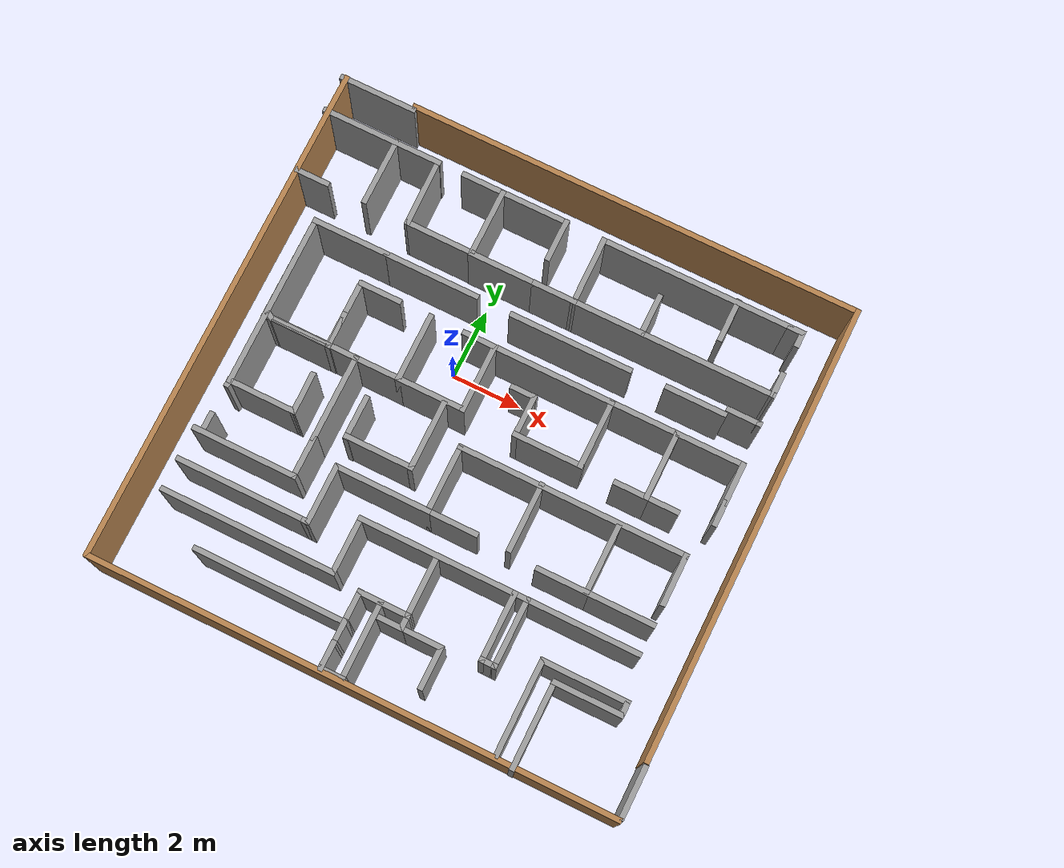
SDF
<?xml version='1.0'?>
<sdf version='1.7'>
  <model name='nidar1'>
    <pose>1.48392 -1.60733 0 0 -0 0</pose>
    <link name='Wall_10'>
      <collision name='Wall_10_Collision'>
        <geometry>
          <box>
            <size>13 0.15 2.5</size>
          </box>
        </geometry>
        <pose>0 0 1.25 0 -0 0</pose>
      </collision>
      <visual name='Wall_10_Visual'>
        <pose>0 0 1.25 0 -0 0</pose>
        <geometry>
          <box>
            <size>13 0.15 2.5</size>
          </box>
        </geometry>
        <material>
          <script>
            <uri>file://media/materials/scripts/gazebo.material</uri>
            <name>Gazebo/Wood</name>
          </script>
          <ambient>1 1 1 1</ambient>
        </material>
        <meta>
          <layer>0</layer>
        </meta>
      </visual>
      <pose>1.04576 7.23235 0 0 -0 3.14159</pose>
    </link>
    <link name='Wall_100'>
      <collision name='Wall_100_Collision'>
        <geometry>
          <box>
            <size>1.25 0.15 2.5</size>
          </box>
        </geometry>
        <pose>0 0 1.25 0 -0 0</pose>
      </collision>
      <visual name='Wall_100_Visual'>
        <pose>0 0 1.25 0 -0 0</pose>
        <geometry>
          <box>
            <size>1.25 0.15 2.5</size>
          </box>
        </geometry>
        <material>
          <script>
            <uri>file://media/materials/scripts/gazebo.material</uri>
            <name>Gazebo/Grey</name>
          </script>
          <ambient>1 1 1 1</ambient>
        </material>
        <meta>
          <layer>0</layer>
        </meta>
      </visual>
      <pose>-3.64531 -2.55736 0 0 -0 -1.5708</pose>
    </link>
    <link name='Wall_101'>
      <collision name='Wall_101_Collision'>
        <geometry>
          <box>
            <size>3 0.15 2.5</size>
          </box>
        </geometry>
        <pose>0 0 1.25 0 -0 0</pose>
      </collision>
      <visual name='Wall_101_Visual'>
        <pose>0 0 1.25 0 -0 0</pose>
        <geometry>
          <box>
            <size>3 0.15 2.5</size>
          </box>
        </geometry>
        <material>
          <script>
            <uri>file://media/materials/scripts/gazebo.material</uri>
            <name>Gazebo/Grey</name>
          </script>
          <ambient>1 1 1 1</ambient>
        </material>
        <meta>
          <layer>0</layer>
        </meta>
      </visual>
      <pose>-5.07031 -3.10737 0 0 -0 3.14159</pose>
    </link>
    <link name='Wall_104'>
      <collision name='Wall_104_Collision'>
        <geometry>
          <box>
            <size>2.75 0.15 2.5</size>
          </box>
        </geometry>
        <pose>0 0 1.25 0 -0 0</pose>
      </collision>
      <visual name='Wall_104_Visual'>
        <pose>0 0 1.25 0 -0 0</pose>
        <geometry>
          <box>
            <size>2.75 0.15 2.5</size>
          </box>
        </geometry>
        <material>
          <script>
            <uri>file://media/materials/scripts/gazebo.material</uri>
            <name>Gazebo/Grey</name>
          </script>
          <ambient>1 1 1 1</ambient>
        </material>
        <meta>
          <layer>0</layer>
        </meta>
      </visual>
      <pose>-2.90001 3.22586 0 0 -0 0</pose>
    </link>
    <link name='Wall_106'>
      <collision name='Wall_106_Collision'>
        <geometry>
          <box>
            <size>3.5 0.15 2.5</size>
          </box>
        </geometry>
        <pose>0 0 1.25 0 -0 0</pose>
      </collision>
      <visual name='Wall_106_Visual'>
        <pose>0 0 1.25 0 -0 0</pose>
        <geometry>
          <box>
            <size>3.5 0.15 2.5</size>
          </box>
        </geometry>
        <material>
          <script>
            <uri>file://media/materials/scripts/gazebo.material</uri>
            <name>Gazebo/Grey</name>
          </script>
          <ambient>1 1 1 1</ambient>
        </material>
        <meta>
          <layer>0</layer>
        </meta>
      </visual>
      <pose>1.15003 3.19392 0 0 -0 0</pose>
    </link>
    <link name='Wall_108'>
      <collision name='Wall_108_Collision'>
        <geometry>
          <box>
            <size>1.75 0.15 2.5</size>
          </box>
        </geometry>
        <pose>0 0 1.25 0 -0 0</pose>
      </collision>
      <visual name='Wall_108_Visual'>
        <pose>0 0 1.25 0 -0 0</pose>
        <geometry>
          <box>
            <size>1.75 0.15 2.5</size>
          </box>
        </geometry>
        <material>
          <script>
            <uri>file://media/materials/scripts/gazebo.material</uri>
            <name>Gazebo/Grey</name>
          </script>
          <ambient>1 1 1 1</ambient>
        </material>
        <meta>
          <layer>0</layer>
        </meta>
      </visual>
      <pose>4.70001 3.21403 0 0 -0 0</pose>
    </link>
    <link name='Wall_110'>
      <collision name='Wall_110_Collision'>
        <geometry>
          <box>
            <size>3.5 0.15 2.5</size>
          </box>
        </geometry>
        <pose>0 0 1.25 0 -0 0</pose>
      </collision>
      <visual name='Wall_110_Visual'>
        <pose>0 0 1.25 0 -0 0</pose>
        <geometry>
          <box>
            <size>3.5 0.15 2.5</size>
          </box>
        </geometry>
        <material>
          <script>
            <uri>file://media/materials/scripts/gazebo.material</uri>
            <name>Gazebo/Grey</name>
          </script>
          <ambient>1 1 1 1</ambient>
        </material>
        <meta>
          <layer>0</layer>
        </meta>
      </visual>
      <pose>1.11152 2.21403 0 0 -0 0</pose>
    </link>
    <link name='Wall_111'>
      <collision name='Wall_111_Collision'>
        <geometry>
          <box>
            <size>2 0.15 2.5</size>
          </box>
        </geometry>
        <pose>0 0 1.25 0 -0 0</pose>
      </collision>
      <visual name='Wall_111_Visual'>
        <pose>0 0 1.25 0 -0 0</pose>
        <geometry>
          <box>
            <size>2 0.15 2.5</size>
          </box>
        </geometry>
        <material>
          <script>
            <uri>file://media/materials/scripts/gazebo.material</uri>
            <name>Gazebo/Grey</name>
          </script>
          <ambient>1 1 1 1</ambient>
        </material>
        <meta>
          <layer>0</layer>
        </meta>
      </visual>
      <pose>2.78652 1.28903 0 0 -0 -1.5708</pose>
    </link>
    <link name='Wall_112'>
      <collision name='Wall_112_Collision'>
        <geometry>
          <box>
            <size>2 0.15 2.5</size>
          </box>
        </geometry>
        <pose>0 0 1.25 0 -0 0</pose>
      </collision>
      <visual name='Wall_112_Visual'>
        <pose>0 0 1.25 0 -0 0</pose>
        <geometry>
          <box>
            <size>2 0.15 2.5</size>
          </box>
        </geometry>
        <material>
          <script>
            <uri>file://media/materials/scripts/gazebo.material</uri>
            <name>Gazebo/Grey</name>
          </script>
          <ambient>1 1 1 1</ambient>
        </material>
        <meta>
          <layer>0</layer>
        </meta>
      </visual>
      <pose>1.86152 0.364029 0 0 -0 3.14159</pose>
    </link>
    <link name='Wall_113'>
      <collision name='Wall_113_Collision'>
        <geometry>
          <box>
            <size>1.25 0.15 2.5</size>
          </box>
        </geometry>
        <pose>0 0 1.25 0 -0 0</pose>
      </collision>
      <visual name='Wall_113_Visual'>
        <pose>0 0 1.25 0 -0 0</pose>
        <geometry>
          <box>
            <size>1.25 0.15 2.5</size>
          </box>
        </geometry>
        <material>
          <script>
            <uri>file://media/materials/scripts/gazebo.material</uri>
            <name>Gazebo/Grey</name>
          </script>
          <ambient>1 1 1 1</ambient>
        </material>
        <meta>
          <layer>0</layer>
        </meta>
      </visual>
      <pose>0.936522 0.914029 0 0 -0 1.5708</pose>
    </link>
    <link name='Wall_114'>
      <collision name='Wall_114_Collision'>
        <geometry>
          <box>
            <size>0.75 0.15 2.5</size>
          </box>
        </geometry>
        <pose>0 0 1.25 0 -0 0</pose>
      </collision>
      <visual name='Wall_114_Visual'>
        <pose>0 0 1.25 0 -0 0</pose>
        <geometry>
          <box>
            <size>0.75 0.15 2.5</size>
          </box>
        </geometry>
        <material>
          <script>
            <uri>file://media/materials/scripts/gazebo.material</uri>
            <name>Gazebo/Grey</name>
          </script>
          <ambient>1 1 1 1</ambient>
        </material>
        <meta>
          <layer>0</layer>
        </meta>
      </visual>
      <pose>0.636522 1.46403 0 0 -0 3.14159</pose>
    </link>
    <link name='Wall_121'>
      <collision name='Wall_121_Collision'>
        <geometry>
          <box>
            <size>3.75 0.15 2.5</size>
          </box>
        </geometry>
        <pose>0 0 1.25 0 -0 0</pose>
      </collision>
      <visual name='Wall_121_Visual'>
        <pose>0 0 1.25 0 -0 0</pose>
        <geometry>
          <box>
            <size>3.75 0.15 2.5</size>
          </box>
        </geometry>
        <material>
          <script>
            <uri>file://media/materials/scripts/gazebo.material</uri>
            <name>Gazebo/Grey</name>
          </script>
          <ambient>1 1 1 1</ambient>
        </material>
        <meta>
          <layer>0</layer>
        </meta>
      </visual>
      <pose>-4.67849 -4.00366 0 0 -0 0</pose>
    </link>
    <link name='Wall_122'>
      <collision name='Wall_122_Collision'>
        <geometry>
          <box>
            <size>0.25 0.15 2.5</size>
          </box>
        </geometry>
        <pose>0 0 1.25 0 -0 0</pose>
      </collision>
      <visual name='Wall_122_Visual'>
        <pose>0 0 1.25 0 -0 0</pose>
        <geometry>
          <box>
            <size>0.25 0.15 2.5</size>
          </box>
        </geometry>
        <material>
          <script>
            <uri>file://media/materials/scripts/gazebo.material</uri>
            <name>Gazebo/Grey</name>
          </script>
          <ambient>1 1 1 1</ambient>
        </material>
        <meta>
          <layer>0</layer>
        </meta>
      </visual>
      <pose>-2.82849 -4.00366 0 0 -0 0</pose>
    </link>
    <link name='Wall_123'>
      <collision name='Wall_123_Collision'>
        <geometry>
          <box>
            <size>1.75 0.15 2.5</size>
          </box>
        </geometry>
        <pose>0 0 1.25 0 -0 0</pose>
      </collision>
      <visual name='Wall_123_Visual'>
        <pose>0 0 1.25 0 -0 0</pose>
        <geometry>
          <box>
            <size>1.75 0.15 2.5</size>
          </box>
        </geometry>
        <material>
          <script>
            <uri>file://media/materials/scripts/gazebo.material</uri>
            <name>Gazebo/Grey</name>
          </script>
          <ambient>1 1 1 1</ambient>
        </material>
        <meta>
          <layer>0</layer>
        </meta>
      </visual>
      <pose>-2.77849 -3.20366 0 0 -0 1.5708</pose>
    </link>
    <link name='Wall_124'>
      <collision name='Wall_124_Collision'>
        <geometry>
          <box>
            <size>2.75 0.15 2.5</size>
          </box>
        </geometry>
        <pose>0 0 1.25 0 -0 0</pose>
      </collision>
      <visual name='Wall_124_Visual'>
        <pose>0 0 1.25 0 -0 0</pose>
        <geometry>
          <box>
            <size>2.75 0.15 2.5</size>
          </box>
        </geometry>
        <material>
          <script>
            <uri>file://media/materials/scripts/gazebo.material</uri>
            <name>Gazebo/Grey</name>
          </script>
          <ambient>1 1 1 1</ambient>
        </material>
        <meta>
          <layer>0</layer>
        </meta>
      </visual>
      <pose>-1.47849 -2.40366 0 0 -0 0</pose>
    </link>
    <link name='Wall_125'>
      <collision name='Wall_125_Collision'>
        <geometry>
          <box>
            <size>2 0.15 2.5</size>
          </box>
        </geometry>
        <pose>0 0 1.25 0 -0 0</pose>
      </collision>
      <visual name='Wall_125_Visual'>
        <pose>0 0 1.25 0 -0 0</pose>
        <geometry>
          <box>
            <size>2 0.15 2.5</size>
          </box>
        </geometry>
        <material>
          <script>
            <uri>file://media/materials/scripts/gazebo.material</uri>
            <name>Gazebo/Grey</name>
          </script>
          <ambient>1 1 1 1</ambient>
        </material>
        <meta>
          <layer>0</layer>
        </meta>
      </visual>
      <pose>-0.178487 -1.47866 0 0 -0 1.5708</pose>
    </link>
    <link name='Wall_126'>
      <collision name='Wall_126_Collision'>
        <geometry>
          <box>
            <size>6.5 0.15 2.5</size>
          </box>
        </geometry>
        <pose>0 0 1.25 0 -0 0</pose>
      </collision>
      <visual name='Wall_126_Visual'>
        <pose>0 0 1.25 0 -0 0</pose>
        <geometry>
          <box>
            <size>6.5 0.15 2.5</size>
          </box>
        </geometry>
        <material>
          <script>
            <uri>file://media/materials/scripts/gazebo.material</uri>
            <name>Gazebo/Grey</name>
          </script>
          <ambient>1 1 1 1</ambient>
        </material>
        <meta>
          <layer>0</layer>
        </meta>
      </visual>
      <pose>2.99651 -0.553664 0 0 -0 0</pose>
    </link>
    <link name='Wall_127'>
      <collision name='Wall_127_Collision'>
        <geometry>
          <box>
            <size>1.5 0.15 2.5</size>
          </box>
        </geometry>
        <pose>0 0 1.25 0 -0 0</pose>
      </collision>
      <visual name='Wall_127_Visual'>
        <pose>0 0 1.25 0 -0 0</pose>
        <geometry>
          <box>
            <size>1.5 0.15 2.5</size>
          </box>
        </geometry>
        <material>
          <script>
            <uri>file://media/materials/scripts/gazebo.material</uri>
            <name>Gazebo/Grey</name>
          </script>
          <ambient>1 1 1 1</ambient>
        </material>
        <meta>
          <layer>0</layer>
        </meta>
      </visual>
      <pose>6.17151 -1.22866 0 0 -0 -1.5708</pose>
    </link>
    <link name='Wall_131'>
      <collision name='Wall_131_Collision'>
        <geometry>
          <box>
            <size>2 0.15 2.5</size>
          </box>
        </geometry>
        <pose>0 0 1.25 0 -0 0</pose>
      </collision>
      <visual name='Wall_131_Visual'>
        <pose>0 0 1.25 0 -0 0</pose>
        <geometry>
          <box>
            <size>2 0.15 2.5</size>
          </box>
        </geometry>
        <material>
          <script>
            <uri>file://media/materials/scripts/gazebo.material</uri>
            <name>Gazebo/Grey</name>
          </script>
          <ambient>1 1 1 1</ambient>
        </material>
        <meta>
          <layer>0</layer>
        </meta>
      </visual>
      <pose>5.24651 -2.50366 0 0 -0 3.14159</pose>
    </link>
    <link name='Wall_133'>
      <collision name='Wall_133_Collision'>
        <geometry>
          <box>
            <size>2 0.15 2.5</size>
          </box>
        </geometry>
        <pose>0 0 1.25 0 -0 0</pose>
      </collision>
      <visual name='Wall_133_Visual'>
        <pose>0 0 1.25 0 -0 0</pose>
        <geometry>
          <box>
            <size>2 0.15 2.5</size>
          </box>
        </geometry>
        <material>
          <script>
            <uri>file://media/materials/scripts/gazebo.material</uri>
            <name>Gazebo/Grey</name>
          </script>
          <ambient>1 1 1 1</ambient>
        </material>
        <meta>
          <layer>0</layer>
        </meta>
      </visual>
      <pose>4.32151 -1.57866 0 0 -0 1.5708</pose>
    </link>
    <link name='Wall_137'>
      <collision name='Wall_137_Collision'>
        <geometry>
          <box>
            <size>7.927 0.15 2.5</size>
          </box>
        </geometry>
        <pose>0 0 1.25 0 -0 0</pose>
      </collision>
      <visual name='Wall_137_Visual'>
        <pose>0 0 1.25 0 -0 0</pose>
        <geometry>
          <box>
            <size>7.927 0.15 2.5</size>
          </box>
        </geometry>
        <material>
          <script>
            <uri>file://media/materials/scripts/gazebo.material</uri>
            <name>Gazebo/Grey</name>
          </script>
          <ambient>1 1 1 1</ambient>
        </material>
        <meta>
          <layer>0</layer>
        </meta>
      </visual>
      <pose>2.27248 -3.32839 0 0 -0 -3.14034</pose>
    </link>
    <link name='Wall_138'>
      <collision name='Wall_138_Collision'>
        <geometry>
          <box>
            <size>1.67818 0.15 2.5</size>
          </box>
        </geometry>
        <pose>0 0 1.25 0 -0 0</pose>
      </collision>
      <visual name='Wall_138_Visual'>
        <pose>0 0 1.25 0 -0 0</pose>
        <geometry>
          <box>
            <size>1.67818 0.15 2.5</size>
          </box>
        </geometry>
        <material>
          <script>
            <uri>file://media/materials/scripts/gazebo.material</uri>
            <name>Gazebo/Grey</name>
          </script>
          <ambient>1 1 1 1</ambient>
        </material>
        <meta>
          <layer>0</layer>
        </meta>
      </visual>
      <pose>-1.61601 -4.11057 0 0 -0 -1.5708</pose>
    </link>
    <link name='Wall_143'>
      <collision name='Wall_143_Collision'>
        <geometry>
          <box>
            <size>2 0.15 2.5</size>
          </box>
        </geometry>
        <pose>0 0 1.25 0 -0 0</pose>
      </collision>
      <visual name='Wall_143_Visual'>
        <pose>0 0 1.25 0 -0 0</pose>
        <geometry>
          <box>
            <size>2 0.15 2.5</size>
          </box>
        </geometry>
        <material>
          <script>
            <uri>file://media/materials/scripts/gazebo.material</uri>
            <name>Gazebo/Grey</name>
          </script>
          <ambient>1 1 1 1</ambient>
        </material>
        <meta>
          <layer>0</layer>
        </meta>
      </visual>
      <pose>3.71152 2.21403 0 0 -0 0</pose>
    </link>
    <link name='Wall_144'>
      <collision name='Wall_144_Collision'>
        <geometry>
          <box>
            <size>2 0.15 2.5</size>
          </box>
        </geometry>
        <pose>0 0 1.25 0 -0 0</pose>
      </collision>
      <visual name='Wall_144_Visual'>
        <pose>0 0 1.25 0 -0 0</pose>
        <geometry>
          <box>
            <size>2 0.15 2.5</size>
          </box>
        </geometry>
        <material>
          <script>
            <uri>file://media/materials/scripts/gazebo.material</uri>
            <name>Gazebo/Grey</name>
          </script>
          <ambient>1 1 1 1</ambient>
        </material>
        <meta>
          <layer>0</layer>
        </meta>
      </visual>
      <pose>4.63652 1.28903 0 0 -0 -1.5708</pose>
    </link>
    <link name='Wall_145'>
      <collision name='Wall_145_Collision'>
        <geometry>
          <box>
            <size>1 0.15 2.5</size>
          </box>
        </geometry>
        <pose>0 0 1.25 0 -0 0</pose>
      </collision>
      <visual name='Wall_145_Visual'>
        <pose>0 0 1.25 0 -0 0</pose>
        <geometry>
          <box>
            <size>1 0.15 2.5</size>
          </box>
        </geometry>
        <material>
          <script>
            <uri>file://media/materials/scripts/gazebo.material</uri>
            <name>Gazebo/Grey</name>
          </script>
          <ambient>1 1 1 1</ambient>
        </material>
        <meta>
          <layer>0</layer>
        </meta>
      </visual>
      <pose>4.21152 0.364029 0 0 -0 3.14159</pose>
    </link>
    <link name='Wall_147'>
      <collision name='Wall_147_Collision'>
        <geometry>
          <box>
            <size>2 0.15 2.5</size>
          </box>
        </geometry>
        <pose>0 0 1.25 0 -0 0</pose>
      </collision>
      <visual name='Wall_147_Visual'>
        <pose>0 0 1.25 0 -0 0</pose>
        <geometry>
          <box>
            <size>2 0.15 2.5</size>
          </box>
        </geometry>
        <material>
          <script>
            <uri>file://media/materials/scripts/gazebo.material</uri>
            <name>Gazebo/Grey</name>
          </script>
          <ambient>1 1 1 1</ambient>
        </material>
        <meta>
          <layer>0</layer>
        </meta>
      </visual>
      <pose>5.56152 2.21403 0 0 -0 0</pose>
    </link>
    <link name='Wall_148'>
      <collision name='Wall_148_Collision'>
        <geometry>
          <box>
            <size>1.25 0.15 2.5</size>
          </box>
        </geometry>
        <pose>0 0 1.25 0 -0 0</pose>
      </collision>
      <visual name='Wall_148_Visual'>
        <pose>0 0 1.25 0 -0 0</pose>
        <geometry>
          <box>
            <size>1.25 0.15 2.5</size>
          </box>
        </geometry>
        <material>
          <script>
            <uri>file://media/materials/scripts/gazebo.material</uri>
            <name>Gazebo/Grey</name>
          </script>
          <ambient>1 1 1 1</ambient>
        </material>
        <meta>
          <layer>0</layer>
        </meta>
      </visual>
      <pose>6.48652 1.66403 0 0 -0 -1.5708</pose>
    </link>
    <link name='Wall_150'>
      <collision name='Wall_150_Collision'>
        <geometry>
          <box>
            <size>1 0.15 2.5</size>
          </box>
        </geometry>
        <pose>0 0 1.25 0 -0 0</pose>
      </collision>
      <visual name='Wall_150_Visual'>
        <pose>0 0 1.25 0 -0 0</pose>
        <geometry>
          <box>
            <size>1 0.15 2.5</size>
          </box>
        </geometry>
        <material>
          <script>
            <uri>file://media/materials/scripts/gazebo.material</uri>
            <name>Gazebo/Grey</name>
          </script>
          <ambient>1 1 1 1</ambient>
        </material>
        <meta>
          <layer>0</layer>
        </meta>
      </visual>
      <pose>5.06152 0.364029 0 0 -0 0</pose>
    </link>
    <link name='Wall_152'>
      <collision name='Wall_152_Collision'>
        <geometry>
          <box>
            <size>0.75 0.15 2.5</size>
          </box>
        </geometry>
        <pose>0 0 1.25 0 -0 0</pose>
      </collision>
      <visual name='Wall_152_Visual'>
        <pose>0 0 1.25 0 -0 0</pose>
        <geometry>
          <box>
            <size>0.75 0.15 2.5</size>
          </box>
        </geometry>
        <material>
          <script>
            <uri>file://media/materials/scripts/gazebo.material</uri>
            <name>Gazebo/Grey</name>
          </script>
          <ambient>1 1 1 1</ambient>
        </material>
        <meta>
          <layer>0</layer>
        </meta>
      </visual>
      <pose>6.48652 0.814029 0 0 -0 -1.5708</pose>
    </link>
    <link name='Wall_154'>
      <collision name='Wall_154_Collision'>
        <geometry>
          <box>
            <size>1.5 0.15 2.5</size>
          </box>
        </geometry>
        <pose>0 0 1.25 0 -0 0</pose>
      </collision>
      <visual name='Wall_154_Visual'>
        <pose>0 0 1.25 0 -0 0</pose>
        <geometry>
          <box>
            <size>1.5 0.15 2.5</size>
          </box>
        </geometry>
        <material>
          <script>
            <uri>file://media/materials/scripts/gazebo.material</uri>
            <name>Gazebo/Grey</name>
          </script>
          <ambient>1 1 1 1</ambient>
        </material>
        <meta>
          <layer>0</layer>
        </meta>
      </visual>
      <pose>0.496513 -2.40366 0 0 -0 0</pose>
    </link>
    <link name='Wall_156'>
      <collision name='Wall_156_Collision'>
        <geometry>
          <box>
            <size>1.5 0.15 2.5</size>
          </box>
        </geometry>
        <pose>0 0 1.25 0 -0 0</pose>
      </collision>
      <visual name='Wall_156_Visual'>
        <pose>0 0 1.25 0 -0 0</pose>
        <geometry>
          <box>
            <size>1.5 0.15 2.5</size>
          </box>
        </geometry>
        <material>
          <script>
            <uri>file://media/materials/scripts/gazebo.material</uri>
            <name>Gazebo/Grey</name>
          </script>
          <ambient>1 1 1 1</ambient>
        </material>
        <meta>
          <layer>0</layer>
        </meta>
      </visual>
      <pose>3.64651 -2.50366 0 0 -0 3.14159</pose>
    </link>
    <link name='Wall_159'>
      <collision name='Wall_159_Collision'>
        <geometry>
          <box>
            <size>2 0.15 2.5</size>
          </box>
        </geometry>
        <pose>0 0 1.25 0 -0 0</pose>
      </collision>
      <visual name='Wall_159_Visual'>
        <pose>0 0 1.25 0 -0 0</pose>
        <geometry>
          <box>
            <size>2 0.15 2.5</size>
          </box>
        </geometry>
        <material>
          <script>
            <uri>file://media/materials/scripts/gazebo.material</uri>
            <name>Gazebo/Grey</name>
          </script>
          <ambient>1 1 1 1</ambient>
        </material>
        <meta>
          <layer>0</layer>
        </meta>
      </visual>
      <pose>2.11079 -1.45942 0 0 -0 -1.5708</pose>
    </link>
    <link name='Wall_167'>
      <collision name='Wall_167_Collision'>
        <geometry>
          <box>
            <size>4.36304 0.15 2.5</size>
          </box>
        </geometry>
        <pose>0 0 1.25 0 -0 0</pose>
      </collision>
      <visual name='Wall_167_Visual'>
        <pose>0 0 1.25 0 -0 0</pose>
        <geometry>
          <box>
            <size>4.36304 0.15 2.5</size>
          </box>
        </geometry>
        <material>
          <script>
            <uri>file://media/materials/scripts/gazebo.material</uri>
            <name>Gazebo/Grey</name>
          </script>
          <ambient>1 1 1 1</ambient>
        </material>
        <meta>
          <layer>0</layer>
        </meta>
      </visual>
      <pose>-2.89355 -5.85839 0 0 -0 0</pose>
    </link>
    <link name='Wall_168'>
      <collision name='Wall_168_Collision'>
        <geometry>
          <box>
            <size>0.982772 0.15 2.5</size>
          </box>
        </geometry>
        <pose>0 0 1.25 0 -0 0</pose>
      </collision>
      <visual name='Wall_168_Visual'>
        <pose>0 0 1.25 0 -0 0</pose>
        <geometry>
          <box>
            <size>0.982772 0.15 2.5</size>
          </box>
        </geometry>
        <material>
          <script>
            <uri>file://media/materials/scripts/gazebo.material</uri>
            <name>Gazebo/Grey</name>
          </script>
          <ambient>1 1 1 1</ambient>
        </material>
        <meta>
          <layer>0</layer>
        </meta>
      </visual>
      <pose>-0.787026 -5.42451 0 0 -0 1.5708</pose>
    </link>
    <link name='Wall_170'>
      <collision name='Wall_170_Collision'>
        <geometry>
          <box>
            <size>1.5 0.15 2.5</size>
          </box>
        </geometry>
        <pose>0 0 1.25 0 -0 0</pose>
      </collision>
      <visual name='Wall_170_Visual'>
        <pose>0 0 1.25 0 -0 0</pose>
        <geometry>
          <box>
            <size>1.5 0.15 2.5</size>
          </box>
        </geometry>
        <material>
          <script>
            <uri>file://media/materials/scripts/gazebo.material</uri>
            <name>Gazebo/Grey</name>
          </script>
          <ambient>1 1 1 1</ambient>
        </material>
        <meta>
          <layer>0</layer>
        </meta>
      </visual>
      <pose>-0.112026 -5.0147 0 0 -0 0</pose>
    </link>
    <link name='Wall_171'>
      <collision name='Wall_171_Collision'>
        <geometry>
          <box>
            <size>1.82725 0.15 2.5</size>
          </box>
        </geometry>
        <pose>0 0 1.25 0 -0 0</pose>
      </collision>
      <visual name='Wall_171_Visual'>
        <pose>0 0 1.25 0 -0 0</pose>
        <geometry>
          <box>
            <size>1.82725 0.15 2.5</size>
          </box>
        </geometry>
        <material>
          <script>
            <uri>file://media/materials/scripts/gazebo.material</uri>
            <name>Gazebo/Grey</name>
          </script>
          <ambient>1 1 1 1</ambient>
        </material>
        <meta>
          <layer>0</layer>
        </meta>
      </visual>
      <pose>0.55803 -4.1761 0 0 -0 1.57669</pose>
    </link>
    <link name='Wall_175'>
      <collision name='Wall_175_Collision'>
        <geometry>
          <box>
            <size>5 0.15 2.5</size>
          </box>
        </geometry>
        <pose>0 0 1.25 0 -0 0</pose>
      </collision>
      <visual name='Wall_175_Visual'>
        <pose>0 0 1.25 0 -0 0</pose>
        <geometry>
          <box>
            <size>5 0.15 2.5</size>
          </box>
        </geometry>
        <material>
          <script>
            <uri>file://media/materials/scripts/gazebo.material</uri>
            <name>Gazebo/Grey</name>
          </script>
          <ambient>1 1 1 1</ambient>
        </material>
        <meta>
          <layer>0</layer>
        </meta>
      </visual>
      <pose>-4.04101 -4.87467 0 0 -0 3.14159</pose>
    </link>
    <link name='Wall_18'>
      <collision name='Wall_18_Collision'>
        <geometry>
          <box>
            <size>3.5 0.15 2.5</size>
          </box>
        </geometry>
        <pose>0 0 1.25 0 -0 0</pose>
      </collision>
      <visual name='Wall_18_Visual'>
        <pose>0 0 1.25 0 -0 0</pose>
        <geometry>
          <box>
            <size>3.5 0.15 2.5</size>
          </box>
        </geometry>
        <material>
          <script>
            <uri>file://media/materials/scripts/gazebo.material</uri>
            <name>Gazebo/Grey</name>
          </script>
          <ambient>1 1 1 1</ambient>
        </material>
        <meta>
          <layer>0</layer>
        </meta>
      </visual>
      <pose>-5.79576 6.09678 0 0 -0 0</pose>
    </link>
    <link name='Wall_181'>
      <collision name='Wall_181_Collision'>
        <geometry>
          <box>
            <size>0.75 0.15 2.5</size>
          </box>
        </geometry>
        <pose>0 0 1.25 0 -0 0</pose>
      </collision>
      <visual name='Wall_181_Visual'>
        <pose>0 0 1.25 0 -0 0</pose>
        <geometry>
          <box>
            <size>0.75 0.15 2.5</size>
          </box>
        </geometry>
        <material>
          <script>
            <uri>file://media/materials/scripts/gazebo.material</uri>
            <name>Gazebo/Grey</name>
          </script>
          <ambient>1 1 1 1</ambient>
        </material>
        <meta>
          <layer>0</layer>
        </meta>
      </visual>
      <pose>-0.787026 -6.1409 0 0 -0 -1.5708</pose>
    </link>
    <link name='Wall_184'>
      <collision name='Wall_184_Collision'>
        <geometry>
          <box>
            <size>2.5 0.15 2.5</size>
          </box>
        </geometry>
        <pose>0 0 1.25 0 -0 0</pose>
      </collision>
      <visual name='Wall_184_Visual'>
        <pose>0 0 1.25 0 -0 0</pose>
        <geometry>
          <box>
            <size>2.5 0.15 2.5</size>
          </box>
        </geometry>
        <material>
          <script>
            <uri>file://media/materials/scripts/gazebo.material</uri>
            <name>Gazebo/Grey</name>
          </script>
          <ambient>1 1 1 1</ambient>
        </material>
        <meta>
          <layer>0</layer>
        </meta>
      </visual>
      <pose>4.57238 -6.05735 0 0 -0 1.5708</pose>
    </link>
    <link name='Wall_185'>
      <collision name='Wall_185_Collision'>
        <geometry>
          <box>
            <size>2 0.15 2.5</size>
          </box>
        </geometry>
        <pose>0 0 1.25 0 -0 0</pose>
      </collision>
      <visual name='Wall_185_Visual'>
        <pose>0 0 1.25 0 -0 0</pose>
        <geometry>
          <box>
            <size>2 0.15 2.5</size>
          </box>
        </geometry>
        <material>
          <script>
            <uri>file://media/materials/scripts/gazebo.material</uri>
            <name>Gazebo/Grey</name>
          </script>
          <ambient>1 1 1 1</ambient>
        </material>
        <meta>
          <layer>0</layer>
        </meta>
      </visual>
      <pose>5.49738 -4.88235 0 0 -0 0</pose>
    </link>
    <link name='Wall_189'>
      <collision name='Wall_189_Collision'>
        <geometry>
          <box>
            <size>0.5 0.15 2.5</size>
          </box>
        </geometry>
        <pose>0 0 1.25 0 -0 0</pose>
      </collision>
      <visual name='Wall_189_Visual'>
        <pose>0 0 1.25 0 -0 0</pose>
        <geometry>
          <box>
            <size>0.5 0.15 2.5</size>
          </box>
        </geometry>
        <material>
          <script>
            <uri>file://media/materials/scripts/gazebo.material</uri>
            <name>Gazebo/Grey</name>
          </script>
          <ambient>1 1 1 1</ambient>
        </material>
        <meta>
          <layer>0</layer>
        </meta>
      </visual>
      <pose>6.42238 -4.70735 0 0 -0 1.5708</pose>
    </link>
    <link name='Wall_19'>
      <collision name='Wall_19_Collision'>
        <geometry>
          <box>
            <size>2 0.15 2.5</size>
          </box>
        </geometry>
        <pose>0 0 1.25 0 -0 0</pose>
      </collision>
      <visual name='Wall_19_Visual'>
        <pose>0 0 1.25 0 -0 0</pose>
        <geometry>
          <box>
            <size>2 0.15 2.5</size>
          </box>
        </geometry>
        <material>
          <script>
            <uri>file://media/materials/scripts/gazebo.material</uri>
            <name>Gazebo/Grey</name>
          </script>
          <ambient>1 1 1 1</ambient>
        </material>
        <meta>
          <layer>0</layer>
        </meta>
      </visual>
      <pose>-4.12076 5.17178 0 0 -0 -1.55189</pose>
    </link>
    <link name='Wall_190'>
      <collision name='Wall_190_Collision'>
        <geometry>
          <box>
            <size>2.5 0.15 2.5</size>
          </box>
        </geometry>
        <pose>0 0 1.25 0 -0 0</pose>
      </collision>
      <visual name='Wall_190_Visual'>
        <pose>0 0 1.25 0 -0 0</pose>
        <geometry>
          <box>
            <size>2.5 0.15 2.5</size>
          </box>
        </geometry>
        <material>
          <script>
            <uri>file://media/materials/scripts/gazebo.material</uri>
            <name>Gazebo/Grey</name>
          </script>
          <ambient>1 1 1 1</ambient>
        </material>
        <meta>
          <layer>0</layer>
        </meta>
      </visual>
      <pose>5.24738 -4.53235 0 0 -0 3.14159</pose>
    </link>
    <link name='Wall_191'>
      <collision name='Wall_191_Collision'>
        <geometry>
          <box>
            <size>2.75 0.15 2.5</size>
          </box>
        </geometry>
        <pose>0 0 1.25 0 -0 0</pose>
      </collision>
      <visual name='Wall_191_Visual'>
        <pose>0 0 1.25 0 -0 0</pose>
        <geometry>
          <box>
            <size>2.75 0.15 2.5</size>
          </box>
        </geometry>
        <material>
          <script>
            <uri>file://media/materials/scripts/gazebo.material</uri>
            <name>Gazebo/Grey</name>
          </script>
          <ambient>1 1 1 1</ambient>
        </material>
        <meta>
          <layer>0</layer>
        </meta>
      </visual>
      <pose>4.07238 -5.83235 0 0 -0 -1.5708</pose>
    </link>
    <link name='Wall_193'>
      <collision name='Wall_193_Collision'>
        <geometry>
          <box>
            <size>2 0.15 2.5</size>
          </box>
        </geometry>
        <pose>0 0 1.25 0 -0 0</pose>
      </collision>
      <visual name='Wall_193_Visual'>
        <pose>0 0 1.25 0 -0 0</pose>
        <geometry>
          <box>
            <size>2 0.15 2.5</size>
          </box>
        </geometry>
        <material>
          <script>
            <uri>file://media/materials/scripts/gazebo.material</uri>
            <name>Gazebo/Grey</name>
          </script>
          <ambient>1 1 1 1</ambient>
        </material>
        <meta>
          <layer>0</layer>
        </meta>
      </visual>
      <pose>2.71844 -4.25707 0 0 -0 -1.5708</pose>
    </link>
    <link name='Wall_194'>
      <collision name='Wall_194_Collision'>
        <geometry>
          <box>
            <size>0.5 0.15 2.5</size>
          </box>
        </geometry>
        <pose>0 0 1.25 0 -0 0</pose>
      </collision>
      <visual name='Wall_194_Visual'>
        <pose>0 0 1.25 0 -0 0</pose>
        <geometry>
          <box>
            <size>0.5 0.15 2.5</size>
          </box>
        </geometry>
        <material>
          <script>
            <uri>file://media/materials/scripts/gazebo.material</uri>
            <name>Gazebo/Grey</name>
          </script>
          <ambient>1 1 1 1</ambient>
        </material>
        <meta>
          <layer>0</layer>
        </meta>
      </visual>
      <pose>2.89344 -5.18207 0 0 -0 0</pose>
    </link>
    <link name='Wall_195'>
      <collision name='Wall_195_Collision'>
        <geometry>
          <box>
            <size>2 0.15 2.5</size>
          </box>
        </geometry>
        <pose>0 0 1.25 0 -0 0</pose>
      </collision>
      <visual name='Wall_195_Visual'>
        <pose>0 0 1.25 0 -0 0</pose>
        <geometry>
          <box>
            <size>2 0.15 2.5</size>
          </box>
        </geometry>
        <material>
          <script>
            <uri>file://media/materials/scripts/gazebo.material</uri>
            <name>Gazebo/Grey</name>
          </script>
          <ambient>1 1 1 1</ambient>
        </material>
        <meta>
          <layer>0</layer>
        </meta>
      </visual>
      <pose>3.06844 -4.25707 0 0 -0 1.5708</pose>
    </link>
    <link name='Wall_197'>
      <collision name='Wall_197_Collision'>
        <geometry>
          <box>
            <size>0.5 0.15 2.5</size>
          </box>
        </geometry>
        <pose>0 0 1.25 0 -0 0</pose>
      </collision>
      <visual name='Wall_197_Visual'>
        <pose>0 0 1.25 0 -0 0</pose>
        <geometry>
          <box>
            <size>0.5 0.15 2.5</size>
          </box>
        </geometry>
        <material>
          <script>
            <uri>file://media/materials/scripts/gazebo.material</uri>
            <name>Gazebo/Grey</name>
          </script>
          <ambient>1 1 1 1</ambient>
        </material>
        <meta>
          <layer>0</layer>
        </meta>
      </visual>
      <pose>0.562974 -5.1897 0 0 -0 -1.5708</pose>
    </link>
    <link name='Wall_198'>
      <collision name='Wall_198_Collision'>
        <geometry>
          <box>
            <size>1.25 0.15 2.5</size>
          </box>
        </geometry>
        <pose>0 0 1.25 0 -0 0</pose>
      </collision>
      <visual name='Wall_198_Visual'>
        <pose>0 0 1.25 0 -0 0</pose>
        <geometry>
          <box>
            <size>1.25 0.15 2.5</size>
          </box>
        </geometry>
        <material>
          <script>
            <uri>file://media/materials/scripts/gazebo.material</uri>
            <name>Gazebo/Grey</name>
          </script>
          <ambient>1 1 1 1</ambient>
        </material>
        <meta>
          <layer>0</layer>
        </meta>
      </visual>
      <pose>1.11297 -5.3647 0 0 -0 0</pose>
    </link>
    <link name='Wall_199'>
      <collision name='Wall_199_Collision'>
        <geometry>
          <box>
            <size>1.25 0.15 2.5</size>
          </box>
        </geometry>
        <pose>0 0 1.25 0 -0 0</pose>
      </collision>
      <visual name='Wall_199_Visual'>
        <pose>0 0 1.25 0 -0 0</pose>
        <geometry>
          <box>
            <size>1.25 0.15 2.5</size>
          </box>
        </geometry>
        <material>
          <script>
            <uri>file://media/materials/scripts/gazebo.material</uri>
            <name>Gazebo/Grey</name>
          </script>
          <ambient>1 1 1 1</ambient>
        </material>
        <meta>
          <layer>0</layer>
        </meta>
      </visual>
      <pose>1.66297 -5.9147 0 0 -0 -1.5708</pose>
    </link>
    <link name='Wall_20'>
      <collision name='Wall_20_Collision'>
        <geometry>
          <box>
            <size>2.02788 0.15 2.5</size>
          </box>
        </geometry>
        <pose>0 0 1.25 0 -0 0</pose>
      </collision>
      <visual name='Wall_20_Visual'>
        <pose>0 0 1.25 0 -0 0</pose>
        <geometry>
          <box>
            <size>2.02788 0.15 2.5</size>
          </box>
        </geometry>
        <material>
          <script>
            <uri>file://media/materials/scripts/gazebo.material</uri>
            <name>Gazebo/Grey</name>
          </script>
          <ambient>1 1 1 1</ambient>
        </material>
        <meta>
          <layer>0</layer>
        </meta>
      </visual>
      <pose>-3.16469 4.24354 0 0 -0 -0.003456</pose>
    </link>
    <link name='Wall_201'>
      <collision name='Wall_201_Collision'>
        <geometry>
          <box>
            <size>2.25 0.15 2.5</size>
          </box>
        </geometry>
        <pose>0 0 1.25 0 -0 0</pose>
      </collision>
      <visual name='Wall_201_Visual'>
        <pose>0 0 1.25 0 -0 0</pose>
        <geometry>
          <box>
            <size>2.25 0.15 2.5</size>
          </box>
        </geometry>
        <material>
          <script>
            <uri>file://media/materials/scripts/gazebo.material</uri>
            <name>Gazebo/Grey</name>
          </script>
          <ambient>1 1 1 1</ambient>
        </material>
        <meta>
          <layer>0</layer>
        </meta>
      </visual>
      <pose>-0.191731 -6.09177 0 0 -0 -1.5708</pose>
    </link>
    <link name='Wall_202'>
      <collision name='Wall_202_Collision'>
        <geometry>
          <box>
            <size>0.75 0.15 2.5</size>
          </box>
        </geometry>
        <pose>0 0 1.25 0 -0 0</pose>
      </collision>
      <visual name='Wall_202_Visual'>
        <pose>0 0 1.25 0 -0 0</pose>
        <geometry>
          <box>
            <size>0.75 0.15 2.5</size>
          </box>
        </geometry>
        <material>
          <script>
            <uri>file://media/materials/scripts/gazebo.material</uri>
            <name>Gazebo/Grey</name>
          </script>
          <ambient>1 1 1 1</ambient>
        </material>
        <meta>
          <layer>0</layer>
        </meta>
      </visual>
      <pose>-0.491731 -7.14177 0 0 -0 3.14159</pose>
    </link>
    <link name='Wall_203'>
      <collision name='Wall_203_Collision'>
        <geometry>
          <box>
            <size>0.850882 0.15 2.5</size>
          </box>
        </geometry>
        <pose>0 0 1.25 0 -0 0</pose>
      </collision>
      <visual name='Wall_203_Visual'>
        <pose>0 0 1.25 0 -0 0</pose>
        <geometry>
          <box>
            <size>0.850882 0.15 2.5</size>
          </box>
        </geometry>
        <material>
          <script>
            <uri>file://media/materials/scripts/gazebo.material</uri>
            <name>Gazebo/Grey</name>
          </script>
          <ambient>1 1 1 1</ambient>
        </material>
        <meta>
          <layer>0</layer>
        </meta>
      </visual>
      <pose>-0.789378 -6.79133 0 0 -0 1.56408</pose>
    </link>
    <link name='Wall_205'>
      <collision name='Wall_205_Collision'>
        <geometry>
          <box>
            <size>0.75 0.15 2.5</size>
          </box>
        </geometry>
        <pose>0 0 1.25 0 -0 0</pose>
      </collision>
      <visual name='Wall_205_Visual'>
        <pose>0 0 1.25 0 -0 0</pose>
        <geometry>
          <box>
            <size>0.75 0.15 2.5</size>
          </box>
        </geometry>
        <material>
          <script>
            <uri>file://media/materials/scripts/gazebo.material</uri>
            <name>Gazebo/Grey</name>
          </script>
          <ambient>1 1 1 1</ambient>
        </material>
        <meta>
          <layer>0</layer>
        </meta>
      </visual>
      <pose>0.262974 -5.3647 0 0 -0 3.14159</pose>
    </link>
    <link name='Wall_21'>
      <collision name='Wall_21_Collision'>
        <geometry>
          <box>
            <size>2 0.15 2.5</size>
          </box>
        </geometry>
        <pose>0 0 1.25 0 -0 0</pose>
      </collision>
      <visual name='Wall_21_Visual'>
        <pose>0 0 1.25 0 -0 0</pose>
        <geometry>
          <box>
            <size>2 0.15 2.5</size>
          </box>
        </geometry>
        <material>
          <script>
            <uri>file://media/materials/scripts/gazebo.material</uri>
            <name>Gazebo/Grey</name>
          </script>
          <ambient>1 1 1 1</ambient>
        </material>
        <meta>
          <layer>0</layer>
        </meta>
      </visual>
      <pose>-2.22612 5.15009 0 0 -0 1.5708</pose>
    </link>
    <link name='Wall_22'>
      <collision name='Wall_22_Collision'>
        <geometry>
          <box>
            <size>1.27717 0.15 2.5</size>
          </box>
        </geometry>
        <pose>0 0 1.25 0 -0 0</pose>
      </collision>
      <visual name='Wall_22_Visual'>
        <pose>0 0 1.25 0 -0 0</pose>
        <geometry>
          <box>
            <size>1.27717 0.15 2.5</size>
          </box>
        </geometry>
        <material>
          <script>
            <uri>file://media/materials/scripts/gazebo.material</uri>
            <name>Gazebo/Grey</name>
          </script>
          <ambient>1 1 1 1</ambient>
        </material>
        <meta>
          <layer>0</layer>
        </meta>
      </visual>
      <pose>-2.78969 6.09354 0 0 -0 3.13584</pose>
    </link>
    <link name='Wall_25'>
      <collision name='Wall_25_Collision'>
        <geometry>
          <box>
            <size>2 0.15 2.5</size>
          </box>
        </geometry>
        <pose>0 0 1.25 0 -0 0</pose>
      </collision>
      <visual name='Wall_25_Visual'>
        <pose>0 0 1.25 0 -0 0</pose>
        <geometry>
          <box>
            <size>2 0.15 2.5</size>
          </box>
        </geometry>
        <material>
          <script>
            <uri>file://media/materials/scripts/gazebo.material</uri>
            <name>Gazebo/Grey</name>
          </script>
          <ambient>1 1 1 1</ambient>
        </material>
        <meta>
          <layer>0</layer>
        </meta>
      </visual>
      <pose>-1.30112 6.0903 0 0 -0 0</pose>
    </link>
    <link name='Wall_26'>
      <collision name='Wall_26_Collision'>
        <geometry>
          <box>
            <size>1.25 0.15 2.5</size>
          </box>
        </geometry>
        <pose>0 0 1.25 0 -0 0</pose>
      </collision>
      <visual name='Wall_26_Visual'>
        <pose>0 0 1.25 0 -0 0</pose>
        <geometry>
          <box>
            <size>1.25 0.15 2.5</size>
          </box>
        </geometry>
        <material>
          <script>
            <uri>file://media/materials/scripts/gazebo.material</uri>
            <name>Gazebo/Grey</name>
          </script>
          <ambient>1 1 1 1</ambient>
        </material>
        <meta>
          <layer>0</layer>
        </meta>
      </visual>
      <pose>-0.376115 5.5403 0 0 -0 -1.5708</pose>
    </link>
    <link name='Wall_28'>
      <collision name='Wall_28_Collision'>
        <geometry>
          <box>
            <size>2 0.15 2.5</size>
          </box>
        </geometry>
        <pose>0 0 1.25 0 -0 0</pose>
      </collision>
      <visual name='Wall_28_Visual'>
        <pose>0 0 1.25 0 -0 0</pose>
        <geometry>
          <box>
            <size>2 0.15 2.5</size>
          </box>
        </geometry>
        <material>
          <script>
            <uri>file://media/materials/scripts/gazebo.material</uri>
            <name>Gazebo/Grey</name>
          </script>
          <ambient>1 1 1 1</ambient>
        </material>
        <meta>
          <layer>0</layer>
        </meta>
      </visual>
      <pose>-1.30112 4.22509 0 0 -0 0</pose>
    </link>
    <link name='Wall_29'>
      <collision name='Wall_29_Collision'>
        <geometry>
          <box>
            <size>1.27011 0.15 2.5</size>
          </box>
        </geometry>
        <pose>0 0 1.25 0 -0 0</pose>
      </collision>
      <visual name='Wall_29_Visual'>
        <pose>0 0 1.25 0 -0 0</pose>
        <geometry>
          <box>
            <size>1.27011 0.15 2.5</size>
          </box>
        </geometry>
        <material>
          <script>
            <uri>file://media/materials/scripts/gazebo.material</uri>
            <name>Gazebo/Grey</name>
          </script>
          <ambient>1 1 1 1</ambient>
        </material>
        <meta>
          <layer>0</layer>
        </meta>
      </visual>
      <pose>0.183942 4.22509 0 0 -0 0</pose>
    </link>
    <link name='Wall_3'>
      <collision name='Wall_3_Collision'>
        <geometry>
          <box>
            <size>14.5 0.15 2.5</size>
          </box>
        </geometry>
        <pose>0 0 1.25 0 -0 0</pose>
      </collision>
      <visual name='Wall_3_Visual'>
        <pose>0 0 1.25 0 -0 0</pose>
        <geometry>
          <box>
            <size>14.5 0.15 2.5</size>
          </box>
        </geometry>
        <material>
          <script>
            <uri>file://media/materials/scripts/gazebo.material</uri>
            <name>Gazebo/Wood</name>
          </script>
          <ambient>1 1 1 1</ambient>
        </material>
        <meta>
          <layer>0</layer>
        </meta>
      </visual>
      <pose>-7.39338 -0.037008 0 0 -0 -1.5708</pose>
    </link>
    <link name='Wall_30'>
      <collision name='Wall_30_Collision'>
        <geometry>
          <box>
            <size>2.00011 0.15 2.5</size>
          </box>
        </geometry>
        <pose>0 0 1.25 0 -0 0</pose>
      </collision>
      <visual name='Wall_30_Visual'>
        <pose>0 0 1.25 0 -0 0</pose>
        <geometry>
          <box>
            <size>2.00011 0.15 2.5</size>
          </box>
        </geometry>
        <material>
          <script>
            <uri>file://media/materials/scripts/gazebo.material</uri>
            <name>Gazebo/Grey</name>
          </script>
          <ambient>1 1 1 1</ambient>
        </material>
        <meta>
          <layer>0</layer>
        </meta>
      </visual>
      <pose>0.733942 5.15009 0 0 -0 1.58167</pose>
    </link>
    <link name='Wall_31'>
      <collision name='Wall_31_Collision'>
        <geometry>
          <box>
            <size>5.5 0.15 2.5</size>
          </box>
        </geometry>
        <pose>0 0 1.25 0 -0 0</pose>
      </collision>
      <visual name='Wall_31_Visual'>
        <pose>0 0 1.25 0 -0 0</pose>
        <geometry>
          <box>
            <size>5.5 0.15 2.5</size>
          </box>
        </geometry>
        <material>
          <script>
            <uri>file://media/materials/scripts/gazebo.material</uri>
            <name>Gazebo/Grey</name>
          </script>
          <ambient>1 1 1 1</ambient>
        </material>
        <meta>
          <layer>0</layer>
        </meta>
      </visual>
      <pose>3.39888 6.07509 0 0 -0 0</pose>
    </link>
    <link name='Wall_32'>
      <collision name='Wall_32_Collision'>
        <geometry>
          <box>
            <size>0.5 0.15 2.5</size>
          </box>
        </geometry>
        <pose>0 0 1.25 0 -0 0</pose>
      </collision>
      <visual name='Wall_32_Visual'>
        <pose>0 0 1.25 0 -0 0</pose>
        <geometry>
          <box>
            <size>0.5 0.15 2.5</size>
          </box>
        </geometry>
        <material>
          <script>
            <uri>file://media/materials/scripts/gazebo.material</uri>
            <name>Gazebo/Grey</name>
          </script>
          <ambient>1 1 1 1</ambient>
        </material>
        <meta>
          <layer>0</layer>
        </meta>
      </visual>
      <pose>6.24888 6.07509 0 0 -0 0</pose>
    </link>
    <link name='Wall_33'>
      <collision name='Wall_33_Collision'>
        <geometry>
          <box>
            <size>0.5 0.15 2.5</size>
          </box>
        </geometry>
        <pose>0 0 1.25 0 -0 0</pose>
      </collision>
      <visual name='Wall_33_Visual'>
        <pose>0 0 1.25 0 -0 0</pose>
        <geometry>
          <box>
            <size>0.5 0.15 2.5</size>
          </box>
        </geometry>
        <material>
          <script>
            <uri>file://media/materials/scripts/gazebo.material</uri>
            <name>Gazebo/Grey</name>
          </script>
          <ambient>1 1 1 1</ambient>
        </material>
        <meta>
          <layer>0</layer>
        </meta>
      </visual>
      <pose>6.42389 5.90009 0 0 -0 -1.5708</pose>
    </link>
    <link name='Wall_35'>
      <collision name='Wall_35_Collision'>
        <geometry>
          <box>
            <size>5.80131 0.15 2.5</size>
          </box>
        </geometry>
        <pose>0 0 1.25 0 -0 0</pose>
      </collision>
      <visual name='Wall_35_Visual'>
        <pose>0 0 1.25 0 -0 0</pose>
        <geometry>
          <box>
            <size>5.80131 0.15 2.5</size>
          </box>
        </geometry>
        <material>
          <script>
            <uri>file://media/materials/scripts/gazebo.material</uri>
            <name>Gazebo/Grey</name>
          </script>
          <ambient>1 1 1 1</ambient>
        </material>
        <meta>
          <layer>0</layer>
        </meta>
      </visual>
      <pose>3.58977 4.22509 0 0 -0 0</pose>
    </link>
    <link name='Wall_36'>
      <collision name='Wall_36_Collision'>
        <geometry>
          <box>
            <size>0.75 0.15 2.5</size>
          </box>
        </geometry>
        <pose>0 0 1.25 0 -0 0</pose>
      </collision>
      <visual name='Wall_36_Visual'>
        <pose>0 0 1.25 0 -0 0</pose>
        <geometry>
          <box>
            <size>0.75 0.15 2.5</size>
          </box>
        </geometry>
        <material>
          <script>
            <uri>file://media/materials/scripts/gazebo.material</uri>
            <name>Gazebo/Grey</name>
          </script>
          <ambient>1 1 1 1</ambient>
        </material>
        <meta>
          <layer>0</layer>
        </meta>
      </visual>
      <pose>6.4153 4.52509 0 0 -0 1.57119</pose>
    </link>
    <link name='Wall_4'>
      <collision name='Wall_4_Collision'>
        <geometry>
          <box>
            <size>15 0.15 2.5</size>
          </box>
        </geometry>
        <pose>0 0 1.25 0 -0 0</pose>
      </collision>
      <visual name='Wall_4_Visual'>
        <pose>0 0 1.25 0 -0 0</pose>
        <geometry>
          <box>
            <size>15 0.15 2.5</size>
          </box>
        </geometry>
        <material>
          <script>
            <uri>file://media/materials/scripts/gazebo.material</uri>
            <name>Gazebo/Wood</name>
          </script>
          <ambient>1 1 1 1</ambient>
        </material>
        <meta>
          <layer>0</layer>
        </meta>
      </visual>
      <pose>0.031617 -7.21201 0 0 -0 0</pose>
    </link>
    <link name='Wall_45'>
      <collision name='Wall_45_Collision'>
        <geometry>
          <box>
            <size>0.15 0.15 2.5</size>
          </box>
        </geometry>
        <pose>0 0 1.25 0 -0 0</pose>
      </collision>
      <visual name='Wall_45_Visual'>
        <pose>0 0 1.25 0 -0 0</pose>
        <geometry>
          <box>
            <size>0.15 0.15 2.5</size>
          </box>
        </geometry>
        <material>
          <script>
            <uri>file://media/materials/scripts/gazebo.material</uri>
            <name>Gazebo/Grey</name>
          </script>
          <ambient>1 1 1 1</ambient>
        </material>
        <meta>
          <layer>0</layer>
        </meta>
      </visual>
      <pose>6.41542 3.37509 0 0 -0 0</pose>
    </link>
    <link name='Wall_48'>
      <collision name='Wall_48_Collision'>
        <geometry>
          <box>
            <size>2.2402 0.15 2.5</size>
          </box>
        </geometry>
        <pose>0 0 1.25 0 -0 0</pose>
      </collision>
      <visual name='Wall_48_Visual'>
        <pose>0 0 1.25 0 -0 0</pose>
        <geometry>
          <box>
            <size>2.2402 0.15 2.5</size>
          </box>
        </geometry>
        <material>
          <script>
            <uri>file://media/materials/scripts/gazebo.material</uri>
            <name>Gazebo/Grey</name>
          </script>
          <ambient>1 1 1 1</ambient>
        </material>
        <meta>
          <layer>0</layer>
        </meta>
      </visual>
      <pose>-5.24511 3.22259 0 0 -0 -3.13847</pose>
    </link>
    <link name='Wall_51'>
      <collision name='Wall_51_Collision'>
        <geometry>
          <box>
            <size>1 0.15 2.5</size>
          </box>
        </geometry>
        <pose>0 0 1.25 0 -0 0</pose>
      </collision>
      <visual name='Wall_51_Visual'>
        <pose>0 0 1.25 0 -0 0</pose>
        <geometry>
          <box>
            <size>1 0.15 2.5</size>
          </box>
        </geometry>
        <material>
          <script>
            <uri>file://media/materials/scripts/gazebo.material</uri>
            <name>Gazebo/Grey</name>
          </script>
          <ambient>1 1 1 1</ambient>
        </material>
        <meta>
          <layer>0</layer>
        </meta>
      </visual>
      <pose>-6.92657 4.2635 0 0 -0 0</pose>
    </link>
    <link name='Wall_53'>
      <collision name='Wall_53_Collision'>
        <geometry>
          <box>
            <size>2 0.15 2.5</size>
          </box>
        </geometry>
        <pose>0 0 1.25 0 -0 0</pose>
      </collision>
      <visual name='Wall_53_Visual'>
        <pose>0 0 1.25 0 -0 0</pose>
        <geometry>
          <box>
            <size>2 0.15 2.5</size>
          </box>
        </geometry>
        <material>
          <script>
            <uri>file://media/materials/scripts/gazebo.material</uri>
            <name>Gazebo/Grey</name>
          </script>
          <ambient>1 1 1 1</ambient>
        </material>
        <meta>
          <layer>0</layer>
        </meta>
      </visual>
      <pose>-5.38321 5.207 0 0 -0 1.5708</pose>
    </link>
    <link name='Wall_56'>
      <collision name='Wall_56_Collision'>
        <geometry>
          <box>
            <size>1.25 0.15 2.5</size>
          </box>
        </geometry>
        <pose>0 0 1.25 0 -0 0</pose>
      </collision>
      <visual name='Wall_56_Visual'>
        <pose>0 0 1.25 0 -0 0</pose>
        <geometry>
          <box>
            <size>1.25 0.15 2.5</size>
          </box>
        </geometry>
        <material>
          <script>
            <uri>file://media/materials/scripts/gazebo.material</uri>
            <name>Gazebo/Grey</name>
          </script>
          <ambient>1 1 1 1</ambient>
        </material>
        <meta>
          <layer>0</layer>
        </meta>
      </visual>
      <pose>4.57677 5.54563 0 0 -0 -1.5708</pose>
    </link>
    <link name='Wall_60'>
      <collision name='Wall_60_Collision'>
        <geometry>
          <box>
            <size>1.25 0.15 2.5</size>
          </box>
        </geometry>
        <pose>0 0 1.25 0 -0 0</pose>
      </collision>
      <visual name='Wall_60_Visual'>
        <pose>0 0 1.25 0 -0 0</pose>
        <geometry>
          <box>
            <size>1.25 0.15 2.5</size>
          </box>
        </geometry>
        <material>
          <script>
            <uri>file://media/materials/scripts/gazebo.material</uri>
            <name>Gazebo/Grey</name>
          </script>
          <ambient>1 1 1 1</ambient>
        </material>
        <meta>
          <layer>0</layer>
        </meta>
      </visual>
      <pose>2.68677 4.77564 0 0 -0 1.5708</pose>
    </link>
    <link name='Wall_62'>
      <collision name='Wall_62_Collision'>
        <geometry>
          <box>
            <size>4.97484 0.15 2.5</size>
          </box>
        </geometry>
        <pose>0 0 1.25 0 -0 0</pose>
      </collision>
      <visual name='Wall_62_Visual'>
        <pose>0 0 1.25 0 -0 0</pose>
        <geometry>
          <box>
            <size>4.97484 0.15 2.5</size>
          </box>
        </geometry>
        <material>
          <script>
            <uri>file://media/materials/scripts/gazebo.material</uri>
            <name>Gazebo/Grey</name>
          </script>
          <ambient>1 1 1 1</ambient>
        </material>
        <meta>
          <layer>0</layer>
        </meta>
      </visual>
      <pose>-6.28359 0.806907 0 0 -0 -1.56805</pose>
    </link>
    <link name='Wall_63'>
      <collision name='Wall_63_Collision'>
        <geometry>
          <box>
            <size>2 0.15 2.5</size>
          </box>
        </geometry>
        <pose>0 0 1.25 0 -0 0</pose>
      </collision>
      <visual name='Wall_63_Visual'>
        <pose>0 0 1.25 0 -0 0</pose>
        <geometry>
          <box>
            <size>2 0.15 2.5</size>
          </box>
        </geometry>
        <material>
          <script>
            <uri>file://media/materials/scripts/gazebo.material</uri>
            <name>Gazebo/Grey</name>
          </script>
          <ambient>1 1 1 1</ambient>
        </material>
        <meta>
          <layer>0</layer>
        </meta>
      </visual>
      <pose>-5.3652 -1.60551 0 0 -0 0</pose>
    </link>
    <link name='Wall_64'>
      <collision name='Wall_64_Collision'>
        <geometry>
          <box>
            <size>1.22491 0.15 2.5</size>
          </box>
        </geometry>
        <pose>0 0 1.25 0 -0 0</pose>
      </collision>
      <visual name='Wall_64_Visual'>
        <pose>0 0 1.25 0 -0 0</pose>
        <geometry>
          <box>
            <size>1.22491 0.15 2.5</size>
          </box>
        </geometry>
        <material>
          <script>
            <uri>file://media/materials/scripts/gazebo.material</uri>
            <name>Gazebo/Grey</name>
          </script>
          <ambient>1 1 1 1</ambient>
        </material>
        <meta>
          <layer>0</layer>
        </meta>
      </visual>
      <pose>-4.43359 -1.06809 0 0 -0 1.5831</pose>
    </link>
    <link name='Wall_66'>
      <collision name='Wall_66_Collision'>
        <geometry>
          <box>
            <size>1.75 0.15 2.5</size>
          </box>
        </geometry>
        <pose>0 0 1.25 0 -0 0</pose>
      </collision>
      <visual name='Wall_66_Visual'>
        <pose>0 0 1.25 0 -0 0</pose>
        <geometry>
          <box>
            <size>1.75 0.15 2.5</size>
          </box>
        </geometry>
        <material>
          <script>
            <uri>file://media/materials/scripts/gazebo.material</uri>
            <name>Gazebo/Grey</name>
          </script>
          <ambient>1 1 1 1</ambient>
        </material>
        <meta>
          <layer>0</layer>
        </meta>
      </visual>
      <pose>-5.31348 0.364029 0 0 -0 3.14159</pose>
    </link>
    <link name='Wall_67'>
      <collision name='Wall_67_Collision'>
        <geometry>
          <box>
            <size>0.25 0.15 2.5</size>
          </box>
        </geometry>
        <pose>0 0 1.25 0 -0 0</pose>
      </collision>
      <visual name='Wall_67_Visual'>
        <pose>0 0 1.25 0 -0 0</pose>
        <geometry>
          <box>
            <size>0.25 0.15 2.5</size>
          </box>
        </geometry>
        <material>
          <script>
            <uri>file://media/materials/scripts/gazebo.material</uri>
            <name>Gazebo/Grey</name>
          </script>
          <ambient>1 1 1 1</ambient>
        </material>
        <meta>
          <layer>0</layer>
        </meta>
      </visual>
      <pose>-6.15678 0.389029 0 0 -0 2.61799</pose>
    </link>
    <link name='Wall_69'>
      <collision name='Wall_69_Collision'>
        <geometry>
          <box>
            <size>3.01994 0.15 2.5</size>
          </box>
        </geometry>
        <pose>0 0 1.25 0 -0 0</pose>
      </collision>
      <visual name='Wall_69_Visual'>
        <pose>0 0 1.25 0 -0 0</pose>
        <geometry>
          <box>
            <size>3.01994 0.15 2.5</size>
          </box>
        </geometry>
        <material>
          <script>
            <uri>file://media/materials/scripts/gazebo.material</uri>
            <name>Gazebo/Grey</name>
          </script>
          <ambient>1 1 1 1</ambient>
        </material>
        <meta>
          <layer>0</layer>
        </meta>
      </visual>
      <pose>-6.2902 1.78459 0 0 -0 -1.5708</pose>
    </link>
    <link name='Wall_70'>
      <collision name='Wall_70_Collision'>
        <geometry>
          <box>
            <size>2 0.15 2.5</size>
          </box>
        </geometry>
        <pose>0 0 1.25 0 -0 0</pose>
      </collision>
      <visual name='Wall_70_Visual'>
        <pose>0 0 1.25 0 -0 0</pose>
        <geometry>
          <box>
            <size>2 0.15 2.5</size>
          </box>
        </geometry>
        <material>
          <script>
            <uri>file://media/materials/scripts/gazebo.material</uri>
            <name>Gazebo/Grey</name>
          </script>
          <ambient>1 1 1 1</ambient>
        </material>
        <meta>
          <layer>0</layer>
        </meta>
      </visual>
      <pose>-5.35198 0.349863 0 0 -0 0</pose>
    </link>
    <link name='Wall_71'>
      <collision name='Wall_71_Collision'>
        <geometry>
          <box>
            <size>2.0202 0.15 2.5</size>
          </box>
        </geometry>
        <pose>0 0 1.25 0 -0 0</pose>
      </collision>
      <visual name='Wall_71_Visual'>
        <pose>0 0 1.25 0 -0 0</pose>
        <geometry>
          <box>
            <size>2.0202 0.15 2.5</size>
          </box>
        </geometry>
        <material>
          <script>
            <uri>file://media/materials/scripts/gazebo.material</uri>
            <name>Gazebo/Grey</name>
          </script>
          <ambient>1 1 1 1</ambient>
        </material>
        <meta>
          <layer>0</layer>
        </meta>
      </visual>
      <pose>-4.4402 1.28459 0 0 -0 1.5708</pose>
    </link>
    <link name='Wall_72'>
      <collision name='Wall_72_Collision'>
        <geometry>
          <box>
            <size>1.25 0.15 2.5</size>
          </box>
        </geometry>
        <pose>0 0 1.25 0 -0 0</pose>
      </collision>
      <visual name='Wall_72_Visual'>
        <pose>0 0 1.25 0 -0 0</pose>
        <geometry>
          <box>
            <size>1.25 0.15 2.5</size>
          </box>
        </geometry>
        <material>
          <script>
            <uri>file://media/materials/scripts/gazebo.material</uri>
            <name>Gazebo/Grey</name>
          </script>
          <ambient>1 1 1 1</ambient>
        </material>
        <meta>
          <layer>0</layer>
        </meta>
      </visual>
      <pose>-3.8902 2.21932 0 0 -0 0</pose>
    </link>
    <link name='Wall_74'>
      <collision name='Wall_74_Collision'>
        <geometry>
          <box>
            <size>2.25 0.15 2.5</size>
          </box>
        </geometry>
        <pose>0 0 1.25 0 -0 0</pose>
      </collision>
      <visual name='Wall_74_Visual'>
        <pose>0 0 1.25 0 -0 0</pose>
        <geometry>
          <box>
            <size>2.25 0.15 2.5</size>
          </box>
        </geometry>
        <material>
          <script>
            <uri>file://media/materials/scripts/gazebo.material</uri>
            <name>Gazebo/Grey</name>
          </script>
          <ambient>1 1 1 1</ambient>
        </material>
        <meta>
          <layer>0</layer>
        </meta>
      </visual>
      <pose>-3.46348 0.364029 0 0 -0 0</pose>
    </link>
    <link name='Wall_75'>
      <collision name='Wall_75_Collision'>
        <geometry>
          <box>
            <size>2 0.15 2.5</size>
          </box>
        </geometry>
        <pose>0 0 1.25 0 -0 0</pose>
      </collision>
      <visual name='Wall_75_Visual'>
        <pose>0 0 1.25 0 -0 0</pose>
        <geometry>
          <box>
            <size>2 0.15 2.5</size>
          </box>
        </geometry>
        <material>
          <script>
            <uri>file://media/materials/scripts/gazebo.material</uri>
            <name>Gazebo/Grey</name>
          </script>
          <ambient>1 1 1 1</ambient>
        </material>
        <meta>
          <layer>0</layer>
        </meta>
      </visual>
      <pose>-2.41348 1.28903 0 0 -0 1.5708</pose>
    </link>
    <link name='Wall_77'>
      <collision name='Wall_77_Collision'>
        <geometry>
          <box>
            <size>1.06955 0.15 2.5</size>
          </box>
        </geometry>
        <pose>0 0 1.25 0 -0 0</pose>
      </collision>
      <visual name='Wall_77_Visual'>
        <pose>0 0 1.25 0 -0 0</pose>
        <geometry>
          <box>
            <size>1.06955 0.15 2.5</size>
          </box>
        </geometry>
        <material>
          <script>
            <uri>file://media/materials/scripts/gazebo.material</uri>
            <name>Gazebo/Grey</name>
          </script>
          <ambient>1 1 1 1</ambient>
        </material>
        <meta>
          <layer>0</layer>
        </meta>
      </visual>
      <pose>-4.4402 0.809591 0 0 -0 1.5708</pose>
    </link>
    <link name='Wall_81'>
      <collision name='Wall_81_Collision'>
        <geometry>
          <box>
            <size>2.5 0.15 2.5</size>
          </box>
        </geometry>
        <pose>0 0 1.25 0 -0 0</pose>
      </collision>
      <visual name='Wall_81_Visual'>
        <pose>0 0 1.25 0 -0 0</pose>
        <geometry>
          <box>
            <size>2.5 0.15 2.5</size>
          </box>
        </geometry>
        <material>
          <script>
            <uri>file://media/materials/scripts/gazebo.material</uri>
            <name>Gazebo/Grey</name>
          </script>
          <ambient>1 1 1 1</ambient>
        </material>
        <meta>
          <layer>0</layer>
        </meta>
      </visual>
      <pose>-3.64531 -0.832365 0 0 -0 -1.5708</pose>
    </link>
    <link name='Wall_84'>
      <collision name='Wall_84_Collision'>
        <geometry>
          <box>
            <size>2 0.15 2.5</size>
          </box>
        </geometry>
        <pose>0 0 1.25 0 -0 0</pose>
      </collision>
      <visual name='Wall_84_Visual'>
        <pose>0 0 1.25 0 -0 0</pose>
        <geometry>
          <box>
            <size>2 0.15 2.5</size>
          </box>
        </geometry>
        <material>
          <script>
            <uri>file://media/materials/scripts/gazebo.material</uri>
            <name>Gazebo/Grey</name>
          </script>
          <ambient>1 1 1 1</ambient>
        </material>
        <meta>
          <layer>0</layer>
        </meta>
      </visual>
      <pose>-1.48848 0.364029 0 0 -0 0</pose>
    </link>
    <link name='Wall_85'>
      <collision name='Wall_85_Collision'>
        <geometry>
          <box>
            <size>2 0.15 2.5</size>
          </box>
        </geometry>
        <pose>0 0 1.25 0 -0 0</pose>
      </collision>
      <visual name='Wall_85_Visual'>
        <pose>0 0 1.25 0 -0 0</pose>
        <geometry>
          <box>
            <size>2 0.15 2.5</size>
          </box>
        </geometry>
        <material>
          <script>
            <uri>file://media/materials/scripts/gazebo.material</uri>
            <name>Gazebo/Grey</name>
          </script>
          <ambient>1 1 1 1</ambient>
        </material>
        <meta>
          <layer>0</layer>
        </meta>
      </visual>
      <pose>-0.563478 1.28903 0 0 -0 1.5708</pose>
    </link>
    <link name='Wall_86'>
      <collision name='Wall_86_Collision'>
        <geometry>
          <box>
            <size>1 0.15 2.5</size>
          </box>
        </geometry>
        <pose>0 0 1.25 0 -0 0</pose>
      </collision>
      <visual name='Wall_86_Visual'>
        <pose>0 0 1.25 0 -0 0</pose>
        <geometry>
          <box>
            <size>1 0.15 2.5</size>
          </box>
        </geometry>
        <material>
          <script>
            <uri>file://media/materials/scripts/gazebo.material</uri>
            <name>Gazebo/Grey</name>
          </script>
          <ambient>1 1 1 1</ambient>
        </material>
        <meta>
          <layer>0</layer>
        </meta>
      </visual>
      <pose>-0.988478 2.21403 0 0 -0 3.14159</pose>
    </link>
    <link name='Wall_88'>
      <collision name='Wall_88_Collision'>
        <geometry>
          <box>
            <size>1.27772 0.15 2.5</size>
          </box>
        </geometry>
        <pose>0 0 1.25 0 -0 0</pose>
      </collision>
      <visual name='Wall_88_Visual'>
        <pose>0 0 1.25 0 -0 0</pose>
        <geometry>
          <box>
            <size>1.27772 0.15 2.5</size>
          </box>
        </geometry>
        <material>
          <script>
            <uri>file://media/materials/scripts/gazebo.material</uri>
            <name>Gazebo/Grey</name>
          </script>
          <ambient>1 1 1 1</ambient>
        </material>
        <meta>
          <layer>0</layer>
        </meta>
      </visual>
      <pose>-2.91646 -1.03808 0 0 -0 -1.5708</pose>
    </link>
    <link name='Wall_89'>
      <collision name='Wall_89_Collision'>
        <geometry>
          <box>
            <size>2 0.15 2.5</size>
          </box>
        </geometry>
        <pose>0 0 1.25 0 -0 0</pose>
      </collision>
      <visual name='Wall_89_Visual'>
        <pose>0 0 1.25 0 -0 0</pose>
        <geometry>
          <box>
            <size>2 0.15 2.5</size>
          </box>
        </geometry>
        <material>
          <script>
            <uri>file://media/materials/scripts/gazebo.material</uri>
            <name>Gazebo/Grey</name>
          </script>
          <ambient>1 1 1 1</ambient>
        </material>
        <meta>
          <layer>0</layer>
        </meta>
      </visual>
      <pose>-1.99146 -1.58871 0 0 -0 0</pose>
    </link>
    <link name='Wall_9'>
      <collision name='Wall_9_Collision'>
        <geometry>
          <box>
            <size>13 0.15 2.5</size>
          </box>
        </geometry>
        <pose>0 0 1.25 0 -0 0</pose>
      </collision>
      <visual name='Wall_9_Visual'>
        <pose>0 0 1.25 0 -0 0</pose>
        <geometry>
          <box>
            <size>13 0.15 2.5</size>
          </box>
        </geometry>
        <material>
          <script>
            <uri>file://media/materials/scripts/gazebo.material</uri>
            <name>Gazebo/Wood</name>
          </script>
          <ambient>1 1 1 1</ambient>
        </material>
        <meta>
          <layer>0</layer>
        </meta>
      </visual>
      <pose>7.47076 0.80735 0 0 -0 1.5708</pose>
    </link>
    <link name='Wall_90'>
      <collision name='Wall_90_Collision'>
        <geometry>
          <box>
            <size>2.02773 0.15 2.5</size>
          </box>
        </geometry>
        <pose>0 0 1.25 0 -0 0</pose>
      </collision>
      <visual name='Wall_90_Visual'>
        <pose>0 0 1.25 0 -0 0</pose>
        <geometry>
          <box>
            <size>2.02773 0.15 2.5</size>
          </box>
        </geometry>
        <material>
          <script>
            <uri>file://media/materials/scripts/gazebo.material</uri>
            <name>Gazebo/Grey</name>
          </script>
          <ambient>1 1 1 1</ambient>
        </material>
        <meta>
          <layer>0</layer>
        </meta>
      </visual>
      <pose>-1.06646 -0.663076 0 0 -0 1.5708</pose>
    </link>
    <link name='Wall_94'>
      <collision name='Wall_94_Collision'>
        <geometry>
          <box>
            <size>1 0.15 2.5</size>
          </box>
        </geometry>
        <pose>0 0 1.25 0 -0 0</pose>
      </collision>
      <visual name='Wall_94_Visual'>
        <pose>0 0 1.25 0 -0 0</pose>
        <geometry>
          <box>
            <size>1 0.15 2.5</size>
          </box>
        </geometry>
        <material>
          <script>
            <uri>file://media/materials/scripts/gazebo.material</uri>
            <name>Gazebo/Grey</name>
          </script>
          <ambient>1 1 1 1</ambient>
        </material>
        <meta>
          <layer>0</layer>
        </meta>
      </visual>
      <pose>5.99042 3.37509 0 0 -0 3.14159</pose>
    </link>
    <link name='Wall_96'>
      <collision name='Wall_96_Collision'>
        <geometry>
          <box>
            <size>0.275872 0.15 2.5</size>
          </box>
        </geometry>
        <pose>0 0 1.25 0 -0 0</pose>
      </collision>
      <visual name='Wall_96_Visual'>
        <pose>0 0 1.25 0 -0 0</pose>
        <geometry>
          <box>
            <size>0.275872 0.15 2.5</size>
          </box>
        </geometry>
        <material>
          <script>
            <uri>file://media/materials/scripts/gazebo.material</uri>
            <name>Gazebo/Grey</name>
          </script>
          <ambient>1 1 1 1</ambient>
        </material>
        <meta>
          <layer>0</layer>
        </meta>
      </visual>
      <pose>-6.28359 -1.66809 0 0 -0 -1.67606</pose>
    </link>
    <link name='Wall_98'>
      <collision name='Wall_98_Collision'>
        <geometry>
          <box>
            <size>0.5 0.15 2.5</size>
          </box>
        </geometry>
        <pose>0 0 1.25 0 -0 0</pose>
      </collision>
      <visual name='Wall_98_Visual'>
        <pose>0 0 1.25 0 -0 0</pose>
        <geometry>
          <box>
            <size>0.5 0.15 2.5</size>
          </box>
        </geometry>
        <material>
          <script>
            <uri>file://media/materials/scripts/gazebo.material</uri>
            <name>Gazebo/Grey</name>
          </script>
          <ambient>1 1 1 1</ambient>
        </material>
        <meta>
          <layer>0</layer>
        </meta>
      </visual>
      <pose>-6.28798 -2.77836 0 0 -0 -1.5708</pose>
    </link>
    <pose>-0.346211 0.278962 0 0 -0 0</pose>
    <link name='Wall_23'>
      <collision name='Wall_23_Collision'>
        <geometry>
          <box>
            <size>2.25 0.15 2.5</size>
          </box>
        </geometry>
        <pose>0 0 1.25 0 -0 0</pose>
      </collision>
      <visual name='Wall_23_Visual'>
        <pose>0 0 1.25 0 -0 0</pose>
        <geometry>
          <box>
            <size>2.25 0.15 2.5</size>
          </box>
        </geometry>
        <material>
          <script>
            <uri>file://media/materials/scripts/gazebo.material</uri>
            <name>Gazebo/Grey</name>
          </script>
          <ambient>1 1 1 1</ambient>
        </material>
        <meta>
          <layer>0</layer>
        </meta>
      </visual>
      <pose>-6.4393 7.12734 0 0 -0 0</pose>
    </link>
    <link name='Wall_29'>
      <collision name='Wall_29_Collision'>
        <geometry>
          <box>
            <size>1.5 0.15 2.5</size>
          </box>
        </geometry>
        <pose>0 0 1.25 0 -0 0</pose>
      </collision>
      <visual name='Wall_29_Visual'>
        <pose>0 0 1.25 0 -0 0</pose>
        <geometry>
          <box>
            <size>1.5 0.15 2.5</size>
          </box>
        </geometry>
        <material>
          <script>
            <uri>file://media/materials/scripts/gazebo.material</uri>
            <name>Gazebo/Grey</name>
          </script>
          <ambient>1 1 1 1</ambient>
        </material>
        <meta>
          <layer>0</layer>
        </meta>
      </visual>
      <pose>7.4893 -6.45234 0 0 -0 -1.5708</pose>
    </link>
    <static>1</static>
  </model>
</sdf>
